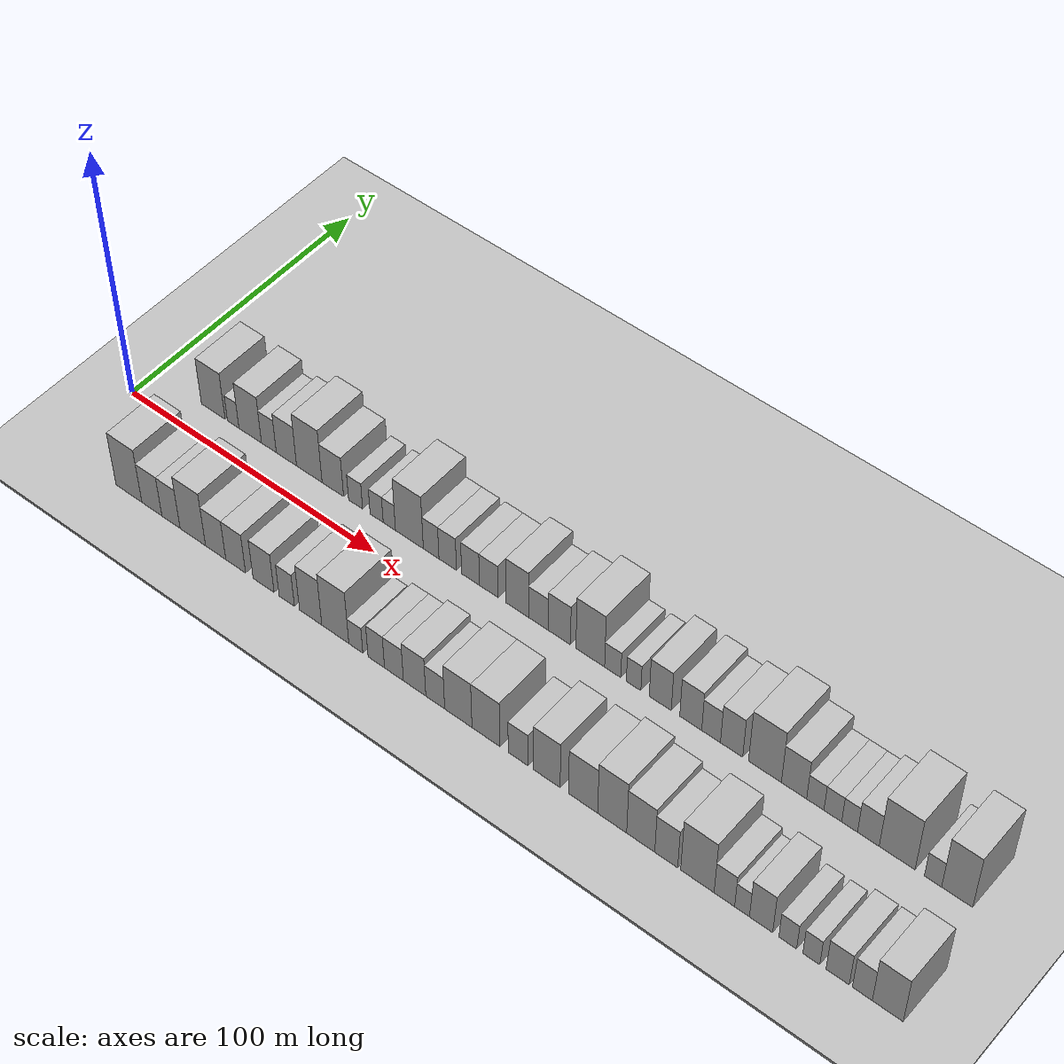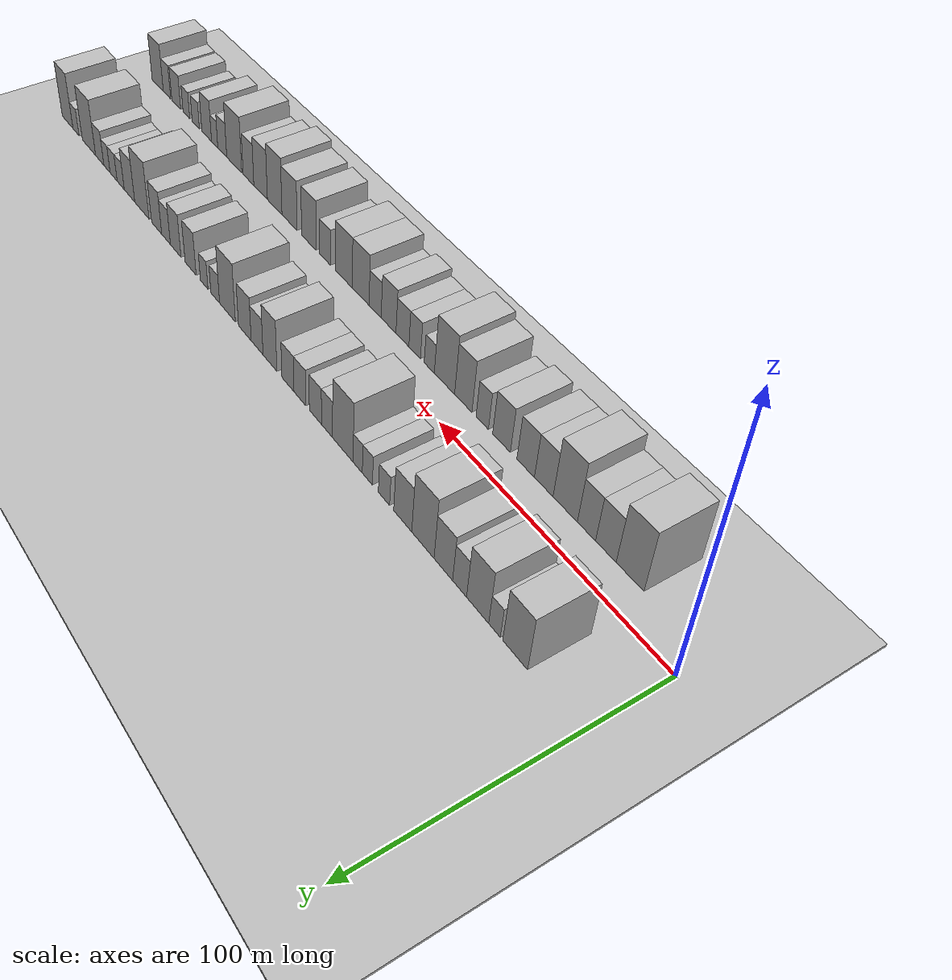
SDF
<?xml version="1.0" encoding="utf-8"?>

<sdf version="1.6">

   <world name="default">

      <gui fullscreen="0">

         <camera name="user_camera">

            <pose>-15 0 4.57585 0 0 0</pose>

            <view_controller>orbit</view_controller>

         </camera>

      </gui>

      <scene>

         <sky>

           <clouds>

             <speed>12</speed>

           </clouds>

         </sky>

         <ambient>0.4 0.4 0.4 1</ambient>

         <background>0.7 0.7 0.7 1</background>

         <shadows>1</shadows>

      </scene>

      <gravity>0 0 -9.8066</gravity>

      <magnetic_field>6e-06 2.3e-05 -4.2e-05</magnetic_field>

      <physics default="0" name="default_physics" type="ode">

         <ode>

            <solver>

               <type>quick</type>

               <iters>10</iters>

               <sor>1.0</sor>

               <use_dynamic_moi_rescaling>0</use_dynamic_moi_rescaling>

            </solver>

            <constraints>

               <cfm>0</cfm>

               <erp>0.2</erp>

               <contact_max_correcting_vel>100</contact_max_correcting_vel>

               <contact_surface_layer>0.001</contact_surface_layer>

            </constraints>

         </ode>

         <max_step_size>0.004</max_step_size>

         <real_time_factor>1</real_time_factor>

         <real_time_update_rate>250</real_time_update_rate>

      </physics>

      <light name="sun" type="directional">

         <cast_shadows>1</cast_shadows>

         <pose>0 0 10 0 0 0</pose>

         <diffuse>0.8 0.8 0.8 1</diffuse>

         <specular>0.2 0.2 0.2 1</specular>

         <attenuation>

            <range>1000</range>

            <constant>0.9</constant>

            <linear>0.01</linear>

            <quadratic>0.001</quadratic>

         </attenuation>

         <direction>-0.5 0.1 -0.9</direction>

      </light>

      <include>

         <name>ground_plane_1</name>

         <uri>model://HANNAS_ground_plane</uri>

         <pose>0 0 0  0 0 0</pose>

      </include>

      <include>

         <name>ground_plane_2</name>

         <uri>model://HANNAS_ground_plane</uri>

         <pose>100 0 0  0 0 0</pose>

      </include>

      <model name="building_1">

         <static>1</static>

         <pose frame="">25.0306 20.0000 0 0.000000 0.000000 1.570796</pose>

         <link name="link">

            <pose frame="">0 0 10.50 0 0 0</pose>

            <collision name="collision">

               <geometry>

                  <box>

                     <size>20.0000 10.0612 21.0000</size>

                  </box>

               </geometry>

               <max_contacts>10</max_contacts>

               <surface>

                  <contact>

                     <ode/>

                  </contact>

                  <bounce/>

                  <friction>

                     <torsional>

                        <ode/>

                     </torsional>

                     <ode/>

                  </friction>

               </surface>

            </collision>

            <visual name="visual">

               <cast_shadows>0</cast_shadows>

               <geometry>

                  <box>

                     <size>20.0000 10.0612 21.0000</size>

                  </box>

               </geometry>

               <material>

                  <script>

                     <uri>model://HANNAS_wall/materials/scripts</uri>

                     <uri>model://HANNAS_wall/materials/textures</uri>

                     <name>vrc/HANNAS_wall</name>

                  </script>

               </material>

            </visual>

            <self_collide>0</self_collide>

            <enable_wind>0</enable_wind>

            <kinematic>0</kinematic>

         </link>

      </model>

      <model name="building_2">

         <static>1</static>

         <pose frame="">33.4875 20.0000 0 0.000000 0.000000 1.570796</pose>

         <link name="link">

            <pose frame="">0 0 6.00 0 0 0</pose>

            <collision name="collision">

               <geometry>

                  <box>

                     <size>20.0000 4.8526 12.0000</size>

                  </box>

               </geometry>

               <max_contacts>10</max_contacts>

               <surface>

                  <contact>

                     <ode/>

                  </contact>

                  <bounce/>

                  <friction>

                     <torsional>

                        <ode/>

                     </torsional>

                     <ode/>

                  </friction>

               </surface>

            </collision>

            <visual name="visual">

               <cast_shadows>0</cast_shadows>

               <geometry>

                  <box>

                     <size>20.0000 4.8526 12.0000</size>

                  </box>

               </geometry>

               <material>

                  <script>

                     <uri>model://HANNAS_wall/materials/scripts</uri>

                     <uri>model://HANNAS_wall/materials/textures</uri>

                     <name>vrc/HANNAS_wall</name>

                  </script>

               </material>

            </visual>

            <self_collide>0</self_collide>

            <enable_wind>0</enable_wind>

            <kinematic>0</kinematic>

         </link>

      </model>

      <model name="building_3">

         <static>1</static>

         <pose frame="">40.6501 20.0000 0 0.000000 0.000000 1.570796</pose>

         <link name="link">

            <pose frame="">0 0 10.50 0 0 0</pose>

            <collision name="collision">

               <geometry>

                  <box>

                     <size>20.0000 9.4726 21.0000</size>

                  </box>

               </geometry>

               <max_contacts>10</max_contacts>

               <surface>

                  <contact>

                     <ode/>

                  </contact>

                  <bounce/>

                  <friction>

                     <torsional>

                        <ode/>

                     </torsional>

                     <ode/>

                  </friction>

               </surface>

            </collision>

            <visual name="visual">

               <cast_shadows>0</cast_shadows>

               <geometry>

                  <box>

                     <size>20.0000 9.4726 21.0000</size>

                  </box>

               </geometry>

               <material>

                  <script>

                     <uri>model://HANNAS_wall/materials/scripts</uri>

                     <uri>model://HANNAS_wall/materials/textures</uri>

                     <name>vrc/HANNAS_wall</name>

                  </script>

               </material>

            </visual>

            <self_collide>0</self_collide>

            <enable_wind>0</enable_wind>

            <kinematic>0</kinematic>

         </link>

      </model>

      <model name="building_4">

         <static>1</static>

         <pose frame="">48.4580 20.0000 0 0.000000 0.000000 1.570796</pose>

         <link name="link">

            <pose frame="">0 0 7.50 0 0 0</pose>

            <collision name="collision">

               <geometry>

                  <box>

                     <size>20.0000 6.1433 15.0000</size>

                  </box>

               </geometry>

               <max_contacts>10</max_contacts>

               <surface>

                  <contact>

                     <ode/>

                  </contact>

                  <bounce/>

                  <friction>

                     <torsional>

                        <ode/>

                     </torsional>

                     <ode/>

                  </friction>

               </surface>

            </collision>

            <visual name="visual">

               <cast_shadows>0</cast_shadows>

               <geometry>

                  <box>

                     <size>20.0000 6.1433 15.0000</size>

                  </box>

               </geometry>

               <material>

                  <script>

                     <uri>model://HANNAS_wall/materials/scripts</uri>

                     <uri>model://HANNAS_wall/materials/textures</uri>

                     <name>vrc/HANNAS_wall</name>

                  </script>

               </material>

            </visual>

            <self_collide>0</self_collide>

            <enable_wind>0</enable_wind>

            <kinematic>0</kinematic>

         </link>

      </model>

      <model name="building_5">

         <static>1</static>

         <pose frame="">55.7201 20.0000 0 0.000000 0.000000 1.570796</pose>

         <link name="link">

            <pose frame="">0 0 9.00 0 0 0</pose>

            <collision name="collision">

               <geometry>

                  <box>

                     <size>20.0000 8.3807 18.0000</size>

                  </box>

               </geometry>

               <max_contacts>10</max_contacts>

               <surface>

                  <contact>

                     <ode/>

                  </contact>

                  <bounce/>

                  <friction>

                     <torsional>

                        <ode/>

                     </torsional>

                     <ode/>

                  </friction>

               </surface>

            </collision>

            <visual name="visual">

               <cast_shadows>0</cast_shadows>

               <geometry>

                  <box>

                     <size>20.0000 8.3807 18.0000</size>

                  </box>

               </geometry>

               <material>

                  <script>

                     <uri>model://HANNAS_wall/materials/scripts</uri>

                     <uri>model://HANNAS_wall/materials/textures</uri>

                     <name>vrc/HANNAS_wall</name>

                  </script>

               </material>

            </visual>

            <self_collide>0</self_collide>

            <enable_wind>0</enable_wind>

            <kinematic>0</kinematic>

         </link>

      </model>

      <model name="building_6">

         <static>1</static>

         <pose frame="">65.1428 20.0000 0 0.000000 0.000000 1.570796</pose>

         <link name="link">

            <pose frame="">0 0 12.00 0 0 0</pose>

            <collision name="collision">

               <geometry>

                  <box>

                     <size>20.0000 10.4647 24.0000</size>

                  </box>

               </geometry>

               <max_contacts>10</max_contacts>

               <surface>

                  <contact>

                     <ode/>

                  </contact>

                  <bounce/>

                  <friction>

                     <torsional>

                        <ode/>

                     </torsional>

                     <ode/>

                  </friction>

               </surface>

            </collision>

            <visual name="visual">

               <cast_shadows>0</cast_shadows>

               <geometry>

                  <box>

                     <size>20.0000 10.4647 24.0000</size>

                  </box>

               </geometry>

               <material>

                  <script>

                     <uri>model://HANNAS_wall/materials/scripts</uri>

                     <uri>model://HANNAS_wall/materials/textures</uri>

                     <name>vrc/HANNAS_wall</name>

                  </script>

               </material>

            </visual>

            <self_collide>0</self_collide>

            <enable_wind>0</enable_wind>

            <kinematic>0</kinematic>

         </link>

      </model>

      <model name="building_7">

         <static>1</static>

         <pose frame="">74.7315 20.0000 0 0.000000 0.000000 1.570796</pose>

         <link name="link">

            <pose frame="">0 0 9.00 0 0 0</pose>

            <collision name="collision">

               <geometry>

                  <box>

                     <size>20.0000 8.7126 18.0000</size>

                  </box>

               </geometry>

               <max_contacts>10</max_contacts>

               <surface>

                  <contact>

                     <ode/>

                  </contact>

                  <bounce/>

                  <friction>

                     <torsional>

                        <ode/>

                     </torsional>

                     <ode/>

                  </friction>

               </surface>

            </collision>

            <visual name="visual">

               <cast_shadows>0</cast_shadows>

               <geometry>

                  <box>

                     <size>20.0000 8.7126 18.0000</size>

                  </box>

               </geometry>

               <material>

                  <script>

                     <uri>model://HANNAS_wall/materials/scripts</uri>

                     <uri>model://HANNAS_wall/materials/textures</uri>

                     <name>vrc/HANNAS_wall</name>

                  </script>

               </material>

            </visual>

            <self_collide>0</self_collide>

            <enable_wind>0</enable_wind>

            <kinematic>0</kinematic>

         </link>

      </model>

      <model name="building_8">

         <static>1</static>

         <pose frame="">83.9068 20.0000 0 0.000000 0.000000 1.570796</pose>

         <link name="link">

            <pose frame="">0 0 6.00 0 0 0</pose>

            <collision name="collision">

               <geometry>

                  <box>

                     <size>20.0000 5.6382 12.0000</size>

                  </box>

               </geometry>

               <max_contacts>10</max_contacts>

               <surface>

                  <contact>

                     <ode/>

                  </contact>

                  <bounce/>

                  <friction>

                     <torsional>

                        <ode/>

                     </torsional>

                     <ode/>

                  </friction>

               </surface>

            </collision>

            <visual name="visual">

               <cast_shadows>0</cast_shadows>

               <geometry>

                  <box>

                     <size>20.0000 5.6382 12.0000</size>

                  </box>

               </geometry>

               <material>

                  <script>

                     <uri>model://HANNAS_wall/materials/scripts</uri>

                     <uri>model://HANNAS_wall/materials/textures</uri>

                     <name>vrc/HANNAS_wall</name>

                  </script>

               </material>

            </visual>

            <self_collide>0</self_collide>

            <enable_wind>0</enable_wind>

            <kinematic>0</kinematic>

         </link>

      </model>

      <model name="building_9">

         <static>1</static>

         <pose frame="">92.3290 20.0000 0 0.000000 0.000000 1.570796</pose>

         <link name="link">

            <pose frame="">0 0 6.00 0 0 0</pose>

            <collision name="collision">

               <geometry>

                  <box>

                     <size>20.0000 5.2062 12.0000</size>

                  </box>

               </geometry>

               <max_contacts>10</max_contacts>

               <surface>

                  <contact>

                     <ode/>

                  </contact>

                  <bounce/>

                  <friction>

                     <torsional>

                        <ode/>

                     </torsional>

                     <ode/>

                  </friction>

               </surface>

            </collision>

            <visual name="visual">

               <cast_shadows>0</cast_shadows>

               <geometry>

                  <box>

                     <size>20.0000 5.2062 12.0000</size>

                  </box>

               </geometry>

               <material>

                  <script>

                     <uri>model://HANNAS_wall/materials/scripts</uri>

                     <uri>model://HANNAS_wall/materials/textures</uri>

                     <name>vrc/HANNAS_wall</name>

                  </script>

               </material>

            </visual>

            <self_collide>0</self_collide>

            <enable_wind>0</enable_wind>

            <kinematic>0</kinematic>

         </link>

      </model>

      <model name="building_10">

         <static>1</static>

         <pose frame="">97.3606 20.0000 0 0.000000 0.000000 1.570796</pose>

         <link name="link">

            <pose frame="">0 0 6.00 0 0 0</pose>

            <collision name="collision">

               <geometry>

                  <box>

                     <size>20.0000 4.8569 12.0000</size>

                  </box>

               </geometry>

               <max_contacts>10</max_contacts>

               <surface>

                  <contact>

                     <ode/>

                  </contact>

                  <bounce/>

                  <friction>

                     <torsional>

                        <ode/>

                     </torsional>

                     <ode/>

                  </friction>

               </surface>

            </collision>

            <visual name="visual">

               <cast_shadows>0</cast_shadows>

               <geometry>

                  <box>

                     <size>20.0000 4.8569 12.0000</size>

                  </box>

               </geometry>

               <material>

                  <script>

                     <uri>model://HANNAS_wall/materials/scripts</uri>

                     <uri>model://HANNAS_wall/materials/textures</uri>

                     <name>vrc/HANNAS_wall</name>

                  </script>

               </material>

            </visual>

            <self_collide>0</self_collide>

            <enable_wind>0</enable_wind>

            <kinematic>0</kinematic>

         </link>

      </model>

      <model name="building_11">

         <static>1</static>

         <pose frame="">105.2721 20.0000 0 0.000000 0.000000 1.570796</pose>

         <link name="link">

            <pose frame="">0 0 12.00 0 0 0</pose>

            <collision name="collision">

               <geometry>

                  <box>

                     <size>20.0000 10.9661 24.0000</size>

                  </box>

               </geometry>

               <max_contacts>10</max_contacts>

               <surface>

                  <contact>

                     <ode/>

                  </contact>

                  <bounce/>

                  <friction>

                     <torsional>

                        <ode/>

                     </torsional>

                     <ode/>

                  </friction>

               </surface>

            </collision>

            <visual name="visual">

               <cast_shadows>0</cast_shadows>

               <geometry>

                  <box>

                     <size>20.0000 10.9661 24.0000</size>

                  </box>

               </geometry>

               <material>

                  <script>

                     <uri>model://HANNAS_wall/materials/scripts</uri>

                     <uri>model://HANNAS_wall/materials/textures</uri>

                     <name>vrc/HANNAS_wall</name>

                  </script>

               </material>

            </visual>

            <self_collide>0</self_collide>

            <enable_wind>0</enable_wind>

            <kinematic>0</kinematic>

         </link>

      </model>

      <model name="building_12">

         <static>1</static>

         <pose frame="">113.7938 20.0000 0 0.000000 0.000000 1.570796</pose>

         <link name="link">

            <pose frame="">0 0 7.50 0 0 0</pose>

            <collision name="collision">

               <geometry>

                  <box>

                     <size>20.0000 6.0773 15.0000</size>

                  </box>

               </geometry>

               <max_contacts>10</max_contacts>

               <surface>

                  <contact>

                     <ode/>

                  </contact>

                  <bounce/>

                  <friction>

                     <torsional>

                        <ode/>

                     </torsional>

                     <ode/>

                  </friction>

               </surface>

            </collision>

            <visual name="visual">

               <cast_shadows>0</cast_shadows>

               <geometry>

                  <box>

                     <size>20.0000 6.0773 15.0000</size>

                  </box>

               </geometry>

               <material>

                  <script>

                     <uri>model://HANNAS_wall/materials/scripts</uri>

                     <uri>model://HANNAS_wall/materials/textures</uri>

                     <name>vrc/HANNAS_wall</name>

                  </script>

               </material>

            </visual>

            <self_collide>0</self_collide>

            <enable_wind>0</enable_wind>

            <kinematic>0</kinematic>

         </link>

      </model>

      <model name="building_13">

         <static>1</static>

         <pose frame="">120.2307 20.0000 0 0.000000 0.000000 1.570796</pose>

         <link name="link">

            <pose frame="">0 0 7.50 0 0 0</pose>

            <collision name="collision">

               <geometry>

                  <box>

                     <size>20.0000 6.7966 15.0000</size>

                  </box>

               </geometry>

               <max_contacts>10</max_contacts>

               <surface>

                  <contact>

                     <ode/>

                  </contact>

                  <bounce/>

                  <friction>

                     <torsional>

                        <ode/>

                     </torsional>

                     <ode/>

                  </friction>

               </surface>

            </collision>

            <visual name="visual">

               <cast_shadows>0</cast_shadows>

               <geometry>

                  <box>

                     <size>20.0000 6.7966 15.0000</size>

                  </box>

               </geometry>

               <material>

                  <script>

                     <uri>model://HANNAS_wall/materials/scripts</uri>

                     <uri>model://HANNAS_wall/materials/textures</uri>

                     <name>vrc/HANNAS_wall</name>

                  </script>

               </material>

            </visual>

            <self_collide>0</self_collide>

            <enable_wind>0</enable_wind>

            <kinematic>0</kinematic>

         </link>

      </model>

      <model name="building_14">

         <static>1</static>

         <pose frame="">129.0535 20.0000 0 0.000000 0.000000 1.570796</pose>

         <link name="link">

            <pose frame="">0 0 7.50 0 0 0</pose>

            <collision name="collision">

               <geometry>

                  <box>

                     <size>20.0000 6.8490 15.0000</size>

                  </box>

               </geometry>

               <max_contacts>10</max_contacts>

               <surface>

                  <contact>

                     <ode/>

                  </contact>

                  <bounce/>

                  <friction>

                     <torsional>

                        <ode/>

                     </torsional>

                     <ode/>

                  </friction>

               </surface>

            </collision>

            <visual name="visual">

               <cast_shadows>0</cast_shadows>

               <geometry>

                  <box>

                     <size>20.0000 6.8490 15.0000</size>

                  </box>

               </geometry>

               <material>

                  <script>

                     <uri>model://HANNAS_wall/materials/scripts</uri>

                     <uri>model://HANNAS_wall/materials/textures</uri>

                     <name>vrc/HANNAS_wall</name>

                  </script>

               </material>

            </visual>

            <self_collide>0</self_collide>

            <enable_wind>0</enable_wind>

            <kinematic>0</kinematic>

         </link>

      </model>

      <model name="building_15">

         <static>1</static>

         <pose frame="">136.0422 20.0000 0 0.000000 0.000000 1.570796</pose>

         <link name="link">

            <pose frame="">0 0 7.50 0 0 0</pose>

            <collision name="collision">

               <geometry>

                  <box>

                     <size>20.0000 7.1284 15.0000</size>

                  </box>

               </geometry>

               <max_contacts>10</max_contacts>

               <surface>

                  <contact>

                     <ode/>

                  </contact>

                  <bounce/>

                  <friction>

                     <torsional>

                        <ode/>

                     </torsional>

                     <ode/>

                  </friction>

               </surface>

            </collision>

            <visual name="visual">

               <cast_shadows>0</cast_shadows>

               <geometry>

                  <box>

                     <size>20.0000 7.1284 15.0000</size>

                  </box>

               </geometry>

               <material>

                  <script>

                     <uri>model://HANNAS_wall/materials/scripts</uri>

                     <uri>model://HANNAS_wall/materials/textures</uri>

                     <name>vrc/HANNAS_wall</name>

                  </script>

               </material>

            </visual>

            <self_collide>0</self_collide>

            <enable_wind>0</enable_wind>

            <kinematic>0</kinematic>

         </link>

      </model>

      <model name="building_16">

         <static>1</static>

         <pose frame="">146.8464 20.0000 0 0.000000 0.000000 1.570796</pose>

         <link name="link">

            <pose frame="">0 0 10.50 0 0 0</pose>

            <collision name="collision">

               <geometry>

                  <box>

                     <size>20.0000 8.4800 21.0000</size>

                  </box>

               </geometry>

               <max_contacts>10</max_contacts>

               <surface>

                  <contact>

                     <ode/>

                  </contact>

                  <bounce/>

                  <friction>

                     <torsional>

                        <ode/>

                     </torsional>

                     <ode/>

                  </friction>

               </surface>

            </collision>

            <visual name="visual">

               <cast_shadows>0</cast_shadows>

               <geometry>

                  <box>

                     <size>20.0000 8.4800 21.0000</size>

                  </box>

               </geometry>

               <material>

                  <script>

                     <uri>model://HANNAS_wall/materials/scripts</uri>

                     <uri>model://HANNAS_wall/materials/textures</uri>

                     <name>vrc/HANNAS_wall</name>

                  </script>

               </material>

            </visual>

            <self_collide>0</self_collide>

            <enable_wind>0</enable_wind>

            <kinematic>0</kinematic>

         </link>

      </model>

      <model name="building_17">

         <static>1</static>

         <pose frame="">154.7855 20.0000 0 0.000000 0.000000 1.570796</pose>

         <link name="link">

            <pose frame="">0 0 7.50 0 0 0</pose>

            <collision name="collision">

               <geometry>

                  <box>

                     <size>20.0000 7.3981 15.0000</size>

                  </box>

               </geometry>

               <max_contacts>10</max_contacts>

               <surface>

                  <contact>

                     <ode/>

                  </contact>

                  <bounce/>

                  <friction>

                     <torsional>

                        <ode/>

                     </torsional>

                     <ode/>

                  </friction>

               </surface>

            </collision>

            <visual name="visual">

               <cast_shadows>0</cast_shadows>

               <geometry>

                  <box>

                     <size>20.0000 7.3981 15.0000</size>

                  </box>

               </geometry>

               <material>

                  <script>

                     <uri>model://HANNAS_wall/materials/scripts</uri>

                     <uri>model://HANNAS_wall/materials/textures</uri>

                     <name>vrc/HANNAS_wall</name>

                  </script>

               </material>

            </visual>

            <self_collide>0</self_collide>

            <enable_wind>0</enable_wind>

            <kinematic>0</kinematic>

         </link>

      </model>

      <model name="building_18">

         <static>1</static>

         <pose frame="">162.5635 20.0000 0 0.000000 0.000000 1.570796</pose>

         <link name="link">

            <pose frame="">0 0 9.00 0 0 0</pose>

            <collision name="collision">

               <geometry>

                  <box>

                     <size>20.0000 8.1580 18.0000</size>

                  </box>

               </geometry>

               <max_contacts>10</max_contacts>

               <surface>

                  <contact>

                     <ode/>

                  </contact>

                  <bounce/>

                  <friction>

                     <torsional>

                        <ode/>

                     </torsional>

                     <ode/>

                  </friction>

               </surface>

            </collision>

            <visual name="visual">

               <cast_shadows>0</cast_shadows>

               <geometry>

                  <box>

                     <size>20.0000 8.1580 18.0000</size>

                  </box>

               </geometry>

               <material>

                  <script>

                     <uri>model://HANNAS_wall/materials/scripts</uri>

                     <uri>model://HANNAS_wall/materials/textures</uri>

                     <name>vrc/HANNAS_wall</name>

                  </script>

               </material>

            </visual>

            <self_collide>0</self_collide>

            <enable_wind>0</enable_wind>

            <kinematic>0</kinematic>

         </link>

      </model>

      <model name="building_19">

         <static>1</static>

         <pose frame="">173.8788 20.0000 0 0.000000 0.000000 1.570796</pose>

         <link name="link">

            <pose frame="">0 0 12.00 0 0 0</pose>

            <collision name="collision">

               <geometry>

                  <box>

                     <size>20.0000 10.4726 24.0000</size>

                  </box>

               </geometry>

               <max_contacts>10</max_contacts>

               <surface>

                  <contact>

                     <ode/>

                  </contact>

                  <bounce/>

                  <friction>

                     <torsional>

                        <ode/>

                     </torsional>

                     <ode/>

                  </friction>

               </surface>

            </collision>

            <visual name="visual">

               <cast_shadows>0</cast_shadows>

               <geometry>

                  <box>

                     <size>20.0000 10.4726 24.0000</size>

                  </box>

               </geometry>

               <material>

                  <script>

                     <uri>model://HANNAS_wall/materials/scripts</uri>

                     <uri>model://HANNAS_wall/materials/textures</uri>

                     <name>vrc/HANNAS_wall</name>

                  </script>

               </material>

            </visual>

            <self_collide>0</self_collide>

            <enable_wind>0</enable_wind>

            <kinematic>0</kinematic>

         </link>

      </model>

      <model name="building_20">

         <static>1</static>

         <pose frame="">182.0511 20.0000 0 0.000000 0.000000 1.570796</pose>

         <link name="link">

            <pose frame="">0 0 6.00 0 0 0</pose>

            <collision name="collision">

               <geometry>

                  <box>

                     <size>20.0000 5.8721 12.0000</size>

                  </box>

               </geometry>

               <max_contacts>10</max_contacts>

               <surface>

                  <contact>

                     <ode/>

                  </contact>

                  <bounce/>

                  <friction>

                     <torsional>

                        <ode/>

                     </torsional>

                     <ode/>

                  </friction>

               </surface>

            </collision>

            <visual name="visual">

               <cast_shadows>0</cast_shadows>

               <geometry>

                  <box>

                     <size>20.0000 5.8721 12.0000</size>

                  </box>

               </geometry>

               <material>

                  <script>

                     <uri>model://HANNAS_wall/materials/scripts</uri>

                     <uri>model://HANNAS_wall/materials/textures</uri>

                     <name>vrc/HANNAS_wall</name>

                  </script>

               </material>

            </visual>

            <self_collide>0</self_collide>

            <enable_wind>0</enable_wind>

            <kinematic>0</kinematic>

         </link>

      </model>

      <model name="building_21">

         <static>1</static>

         <pose frame="">189.6062 20.0000 0 0.000000 0.000000 1.570796</pose>

         <link name="link">

            <pose frame="">0 0 6.00 0 0 0</pose>

            <collision name="collision">

               <geometry>

                  <box>

                     <size>20.0000 5.2382 12.0000</size>

                  </box>

               </geometry>

               <max_contacts>10</max_contacts>

               <surface>

                  <contact>

                     <ode/>

                  </contact>

                  <bounce/>

                  <friction>

                     <torsional>

                        <ode/>

                     </torsional>

                     <ode/>

                  </friction>

               </surface>

            </collision>

            <visual name="visual">

               <cast_shadows>0</cast_shadows>

               <geometry>

                  <box>

                     <size>20.0000 5.2382 12.0000</size>

                  </box>

               </geometry>

               <material>

                  <script>

                     <uri>model://HANNAS_wall/materials/scripts</uri>

                     <uri>model://HANNAS_wall/materials/textures</uri>

                     <name>vrc/HANNAS_wall</name>

                  </script>

               </material>

            </visual>

            <self_collide>0</self_collide>

            <enable_wind>0</enable_wind>

            <kinematic>0</kinematic>

         </link>

      </model>

      <model name="building_22">

         <static>1</static>

         <pose frame="">199.1457 20.0000 0 0.000000 0.000000 1.570796</pose>

         <link name="link">

            <pose frame="">0 0 9.00 0 0 0</pose>

            <collision name="collision">

               <geometry>

                  <box>

                     <size>20.0000 7.8409 18.0000</size>

                  </box>

               </geometry>

               <max_contacts>10</max_contacts>

               <surface>

                  <contact>

                     <ode/>

                  </contact>

                  <bounce/>

                  <friction>

                     <torsional>

                        <ode/>

                     </torsional>

                     <ode/>

                  </friction>

               </surface>

            </collision>

            <visual name="visual">

               <cast_shadows>0</cast_shadows>

               <geometry>

                  <box>

                     <size>20.0000 7.8409 18.0000</size>

                  </box>

               </geometry>

               <material>

                  <script>

                     <uri>model://HANNAS_wall/materials/scripts</uri>

                     <uri>model://HANNAS_wall/materials/textures</uri>

                     <name>vrc/HANNAS_wall</name>

                  </script>

               </material>

            </visual>

            <self_collide>0</self_collide>

            <enable_wind>0</enable_wind>

            <kinematic>0</kinematic>

         </link>

      </model>

      <model name="building_23">

         <static>1</static>

         <pose frame="">209.9331 20.0000 0 0.000000 0.000000 1.570796</pose>

         <link name="link">

            <pose frame="">0 0 9.00 0 0 0</pose>

            <collision name="collision">

               <geometry>

                  <box>

                     <size>20.0000 7.7338 18.0000</size>

                  </box>

               </geometry>

               <max_contacts>10</max_contacts>

               <surface>

                  <contact>

                     <ode/>

                  </contact>

                  <bounce/>

                  <friction>

                     <torsional>

                        <ode/>

                     </torsional>

                     <ode/>

                  </friction>

               </surface>

            </collision>

            <visual name="visual">

               <cast_shadows>0</cast_shadows>

               <geometry>

                  <box>

                     <size>20.0000 7.7338 18.0000</size>

                  </box>

               </geometry>

               <material>

                  <script>

                     <uri>model://HANNAS_wall/materials/scripts</uri>

                     <uri>model://HANNAS_wall/materials/textures</uri>

                     <name>vrc/HANNAS_wall</name>

                  </script>

               </material>

            </visual>

            <self_collide>0</self_collide>

            <enable_wind>0</enable_wind>

            <kinematic>0</kinematic>

         </link>

      </model>

      <model name="building_24">

         <static>1</static>

         <pose frame="">217.0716 20.0000 0 0.000000 0.000000 1.570796</pose>

         <link name="link">

            <pose frame="">0 0 7.50 0 0 0</pose>

            <collision name="collision">

               <geometry>

                  <box>

                     <size>20.0000 6.5432 15.0000</size>

                  </box>

               </geometry>

               <max_contacts>10</max_contacts>

               <surface>

                  <contact>

                     <ode/>

                  </contact>

                  <bounce/>

                  <friction>

                     <torsional>

                        <ode/>

                     </torsional>

                     <ode/>

                  </friction>

               </surface>

            </collision>

            <visual name="visual">

               <cast_shadows>0</cast_shadows>

               <geometry>

                  <box>

                     <size>20.0000 6.5432 15.0000</size>

                  </box>

               </geometry>

               <material>

                  <script>

                     <uri>model://HANNAS_wall/materials/scripts</uri>

                     <uri>model://HANNAS_wall/materials/textures</uri>

                     <name>vrc/HANNAS_wall</name>

                  </script>

               </material>

            </visual>

            <self_collide>0</self_collide>

            <enable_wind>0</enable_wind>

            <kinematic>0</kinematic>

         </link>

      </model>

      <model name="building_25">

         <static>1</static>

         <pose frame="">224.2039 20.0000 0 0.000000 0.000000 1.570796</pose>

         <link name="link">

            <pose frame="">0 0 9.00 0 0 0</pose>

            <collision name="collision">

               <geometry>

                  <box>

                     <size>20.0000 7.7216 18.0000</size>

                  </box>

               </geometry>

               <max_contacts>10</max_contacts>

               <surface>

                  <contact>

                     <ode/>

                  </contact>

                  <bounce/>

                  <friction>

                     <torsional>

                        <ode/>

                     </torsional>

                     <ode/>

                  </friction>

               </surface>

            </collision>

            <visual name="visual">

               <cast_shadows>0</cast_shadows>

               <geometry>

                  <box>

                     <size>20.0000 7.7216 18.0000</size>

                  </box>

               </geometry>

               <material>

                  <script>

                     <uri>model://HANNAS_wall/materials/scripts</uri>

                     <uri>model://HANNAS_wall/materials/textures</uri>

                     <name>vrc/HANNAS_wall</name>

                  </script>

               </material>

            </visual>

            <self_collide>0</self_collide>

            <enable_wind>0</enable_wind>

            <kinematic>0</kinematic>

         </link>

      </model>

      <model name="building_26">

         <static>1</static>

         <pose frame="">235.6873 20.0000 0 0.000000 0.000000 1.570796</pose>

         <link name="link">

            <pose frame="">0 0 12.00 0 0 0</pose>

            <collision name="collision">

               <geometry>

                  <box>

                     <size>20.0000 11.2451 24.0000</size>

                  </box>

               </geometry>

               <max_contacts>10</max_contacts>

               <surface>

                  <contact>

                     <ode/>

                  </contact>

                  <bounce/>

                  <friction>

                     <torsional>

                        <ode/>

                     </torsional>

                     <ode/>

                  </friction>

               </surface>

            </collision>

            <visual name="visual">

               <cast_shadows>0</cast_shadows>

               <geometry>

                  <box>

                     <size>20.0000 11.2451 24.0000</size>

                  </box>

               </geometry>

               <material>

                  <script>

                     <uri>model://HANNAS_wall/materials/scripts</uri>

                     <uri>model://HANNAS_wall/materials/textures</uri>

                     <name>vrc/HANNAS_wall</name>

                  </script>

               </material>

            </visual>

            <self_collide>0</self_collide>

            <enable_wind>0</enable_wind>

            <kinematic>0</kinematic>

         </link>

      </model>

      <model name="building_27">

         <static>1</static>

         <pose frame="">245.5917 20.0000 0 0.000000 0.000000 1.570796</pose>

         <link name="link">

            <pose frame="">0 0 9.00 0 0 0</pose>

            <collision name="collision">

               <geometry>

                  <box>

                     <size>20.0000 8.5637 18.0000</size>

                  </box>

               </geometry>

               <max_contacts>10</max_contacts>

               <surface>

                  <contact>

                     <ode/>

                  </contact>

                  <bounce/>

                  <friction>

                     <torsional>

                        <ode/>

                     </torsional>

                     <ode/>

                  </friction>

               </surface>

            </collision>

            <visual name="visual">

               <cast_shadows>0</cast_shadows>

               <geometry>

                  <box>

                     <size>20.0000 8.5637 18.0000</size>

                  </box>

               </geometry>

               <material>

                  <script>

                     <uri>model://HANNAS_wall/materials/scripts</uri>

                     <uri>model://HANNAS_wall/materials/textures</uri>

                     <name>vrc/HANNAS_wall</name>

                  </script>

               </material>

            </visual>

            <self_collide>0</self_collide>

            <enable_wind>0</enable_wind>

            <kinematic>0</kinematic>

         </link>

      </model>

      <model name="building_28">

         <static>1</static>

         <pose frame="">252.7836 20.0000 0 0.000000 0.000000 1.570796</pose>

         <link name="link">

            <pose frame="">0 0 6.00 0 0 0</pose>

            <collision name="collision">

               <geometry>

                  <box>

                     <size>20.0000 5.8200 12.0000</size>

                  </box>

               </geometry>

               <max_contacts>10</max_contacts>

               <surface>

                  <contact>

                     <ode/>

                  </contact>

                  <bounce/>

                  <friction>

                     <torsional>

                        <ode/>

                     </torsional>

                     <ode/>

                  </friction>

               </surface>

            </collision>

            <visual name="visual">

               <cast_shadows>0</cast_shadows>

               <geometry>

                  <box>

                     <size>20.0000 5.8200 12.0000</size>

                  </box>

               </geometry>

               <material>

                  <script>

                     <uri>model://HANNAS_wall/materials/scripts</uri>

                     <uri>model://HANNAS_wall/materials/textures</uri>

                     <name>vrc/HANNAS_wall</name>

                  </script>

               </material>

            </visual>

            <self_collide>0</self_collide>

            <enable_wind>0</enable_wind>

            <kinematic>0</kinematic>

         </link>

      </model>

      <model name="building_29">

         <static>1</static>

         <pose frame="">258.6537 20.0000 0 0.000000 0.000000 1.570796</pose>

         <link name="link">

            <pose frame="">0 0 6.00 0 0 0</pose>

            <collision name="collision">

               <geometry>

                  <box>

                     <size>20.0000 5.9202 12.0000</size>

                  </box>

               </geometry>

               <max_contacts>10</max_contacts>

               <surface>

                  <contact>

                     <ode/>

                  </contact>

                  <bounce/>

                  <friction>

                     <torsional>

                        <ode/>

                     </torsional>

                     <ode/>

                  </friction>

               </surface>

            </collision>

            <visual name="visual">

               <cast_shadows>0</cast_shadows>

               <geometry>

                  <box>

                     <size>20.0000 5.9202 12.0000</size>

                  </box>

               </geometry>

               <material>

                  <script>

                     <uri>model://HANNAS_wall/materials/scripts</uri>

                     <uri>model://HANNAS_wall/materials/textures</uri>

                     <name>vrc/HANNAS_wall</name>

                  </script>

               </material>

            </visual>

            <self_collide>0</self_collide>

            <enable_wind>0</enable_wind>

            <kinematic>0</kinematic>

         </link>

      </model>

      <model name="building_30">

         <static>1</static>

         <pose frame="">264.2388 20.0000 0 0.000000 0.000000 1.570796</pose>

         <link name="link">

            <pose frame="">0 0 6.00 0 0 0</pose>

            <collision name="collision">

               <geometry>

                  <box>

                     <size>20.0000 5.2501 12.0000</size>

                  </box>

               </geometry>

               <max_contacts>10</max_contacts>

               <surface>

                  <contact>

                     <ode/>

                  </contact>

                  <bounce/>

                  <friction>

                     <torsional>

                        <ode/>

                     </torsional>

                     <ode/>

                  </friction>

               </surface>

            </collision>

            <visual name="visual">

               <cast_shadows>0</cast_shadows>

               <geometry>

                  <box>

                     <size>20.0000 5.2501 12.0000</size>

                  </box>

               </geometry>

               <material>

                  <script>

                     <uri>model://HANNAS_wall/materials/scripts</uri>

                     <uri>model://HANNAS_wall/materials/textures</uri>

                     <name>vrc/HANNAS_wall</name>

                  </script>

               </material>

            </visual>

            <self_collide>0</self_collide>

            <enable_wind>0</enable_wind>

            <kinematic>0</kinematic>

         </link>

      </model>

      <model name="building_31">

         <static>1</static>

         <pose frame="">270.4426 20.0000 0 0.000000 0.000000 1.570796</pose>

         <link name="link">

            <pose frame="">0 0 7.50 0 0 0</pose>

            <collision name="collision">

               <geometry>

                  <box>

                     <size>20.0000 7.1574 15.0000</size>

                  </box>

               </geometry>

               <max_contacts>10</max_contacts>

               <surface>

                  <contact>

                     <ode/>

                  </contact>

                  <bounce/>

                  <friction>

                     <torsional>

                        <ode/>

                     </torsional>

                     <ode/>

                  </friction>

               </surface>

            </collision>

            <visual name="visual">

               <cast_shadows>0</cast_shadows>

               <geometry>

                  <box>

                     <size>20.0000 7.1574 15.0000</size>

                  </box>

               </geometry>

               <material>

                  <script>

                     <uri>model://HANNAS_wall/materials/scripts</uri>

                     <uri>model://HANNAS_wall/materials/textures</uri>

                     <name>vrc/HANNAS_wall</name>

                  </script>

               </material>

            </visual>

            <self_collide>0</self_collide>

            <enable_wind>0</enable_wind>

            <kinematic>0</kinematic>

         </link>

      </model>

      <model name="building_32">

         <static>1</static>

         <pose frame="">279.8806 20.0000 0 0.000000 0.000000 1.570796</pose>

         <link name="link">

            <pose frame="">0 0 12.00 0 0 0</pose>

            <collision name="collision">

               <geometry>

                  <box>

                     <size>20.0000 11.7185 24.0000</size>

                  </box>

               </geometry>

               <max_contacts>10</max_contacts>

               <surface>

                  <contact>

                     <ode/>

                  </contact>

                  <bounce/>

                  <friction>

                     <torsional>

                        <ode/>

                     </torsional>

                     <ode/>

                  </friction>

               </surface>

            </collision>

            <visual name="visual">

               <cast_shadows>0</cast_shadows>

               <geometry>

                  <box>

                     <size>20.0000 11.7185 24.0000</size>

                  </box>

               </geometry>

               <material>

                  <script>

                     <uri>model://HANNAS_wall/materials/scripts</uri>

                     <uri>model://HANNAS_wall/materials/textures</uri>

                     <name>vrc/HANNAS_wall</name>

                  </script>

               </material>

            </visual>

            <self_collide>0</self_collide>

            <enable_wind>0</enable_wind>

            <kinematic>0</kinematic>

         </link>

      </model>

      <model name="building_33">

         <static>1</static>

         <pose frame="">291.5039 20.0000 0 0.000000 0.000000 1.570796</pose>

         <link name="link">

            <pose frame="">0 0 6.00 0 0 0</pose>

            <collision name="collision">

               <geometry>

                  <box>

                     <size>20.0000 5.5281 12.0000</size>

                  </box>

               </geometry>

               <max_contacts>10</max_contacts>

               <surface>

                  <contact>

                     <ode/>

                  </contact>

                  <bounce/>

                  <friction>

                     <torsional>

                        <ode/>

                     </torsional>

                     <ode/>

                  </friction>

               </surface>

            </collision>

            <visual name="visual">

               <cast_shadows>0</cast_shadows>

               <geometry>

                  <box>

                     <size>20.0000 5.5281 12.0000</size>

                  </box>

               </geometry>

               <material>

                  <script>

                     <uri>model://HANNAS_wall/materials/scripts</uri>

                     <uri>model://HANNAS_wall/materials/textures</uri>

                     <name>vrc/HANNAS_wall</name>

                  </script>

               </material>

            </visual>

            <self_collide>0</self_collide>

            <enable_wind>0</enable_wind>

            <kinematic>0</kinematic>

         </link>

      </model>

      <model name="building_34">

         <static>1</static>

         <pose frame="">299.2291 20.0000 0 0.000000 0.000000 1.570796</pose>

         <link name="link">

            <pose frame="">0 0 12.00 0 0 0</pose>

            <collision name="collision">

               <geometry>

                  <box>

                     <size>20.0000 9.9224 24.0000</size>

                  </box>

               </geometry>

               <max_contacts>10</max_contacts>

               <surface>

                  <contact>

                     <ode/>

                  </contact>

                  <bounce/>

                  <friction>

                     <torsional>

                        <ode/>

                     </torsional>

                     <ode/>

                  </friction>

               </surface>

            </collision>

            <visual name="visual">

               <cast_shadows>0</cast_shadows>

               <geometry>

                  <box>

                     <size>20.0000 9.9224 24.0000</size>

                  </box>

               </geometry>

               <material>

                  <script>

                     <uri>model://HANNAS_wall/materials/scripts</uri>

                     <uri>model://HANNAS_wall/materials/textures</uri>

                     <name>vrc/HANNAS_wall</name>

                  </script>

               </material>

            </visual>

            <self_collide>0</self_collide>

            <enable_wind>0</enable_wind>

            <kinematic>0</kinematic>

         </link>

      </model>

      <model name="building_35">

         <static>1</static>

         <pose frame="">28.4641 -20.0000 0 0.000000 0.000000 1.570796</pose>

         <link name="link">

            <pose frame="">0 0 12.00 0 0 0</pose>

            <collision name="collision">

               <geometry>

                  <box>

                     <size>20.0000 10.9283 24.0000</size>

                  </box>

               </geometry>

               <max_contacts>10</max_contacts>

               <surface>

                  <contact>

                     <ode/>

                  </contact>

                  <bounce/>

                  <friction>

                     <torsional>

                        <ode/>

                     </torsional>

                     <ode/>

                  </friction>

               </surface>

            </collision>

            <visual name="visual">

               <cast_shadows>0</cast_shadows>

               <geometry>

                  <box>

                     <size>20.0000 10.9283 24.0000</size>

                  </box>

               </geometry>

               <material>

                  <script>

                     <uri>model://HANNAS_wall/materials/scripts</uri>

                     <uri>model://HANNAS_wall/materials/textures</uri>

                     <name>vrc/HANNAS_wall</name>

                  </script>

               </material>

            </visual>

            <self_collide>0</self_collide>

            <enable_wind>0</enable_wind>

            <kinematic>0</kinematic>

         </link>

      </model>

      <model name="building_36">

         <static>1</static>

         <pose frame="">38.1066 -20.0000 0 0.000000 0.000000 1.570796</pose>

         <link name="link">

            <pose frame="">0 0 9.00 0 0 0</pose>

            <collision name="collision">

               <geometry>

                  <box>

                     <size>20.0000 8.3566 18.0000</size>

                  </box>

               </geometry>

               <max_contacts>10</max_contacts>

               <surface>

                  <contact>

                     <ode/>

                  </contact>

                  <bounce/>

                  <friction>

                     <torsional>

                        <ode/>

                     </torsional>

                     <ode/>

                  </friction>

               </surface>

            </collision>

            <visual name="visual">

               <cast_shadows>0</cast_shadows>

               <geometry>

                  <box>

                     <size>20.0000 8.3566 18.0000</size>

                  </box>

               </geometry>

               <material>

                  <script>

                     <uri>model://HANNAS_wall/materials/scripts</uri>

                     <uri>model://HANNAS_wall/materials/textures</uri>

                     <name>vrc/HANNAS_wall</name>

                  </script>

               </material>

            </visual>

            <self_collide>0</self_collide>

            <enable_wind>0</enable_wind>

            <kinematic>0</kinematic>

         </link>

      </model>

      <model name="building_37">

         <static>1</static>

         <pose frame="">46.0715 -20.0000 0 0.000000 0.000000 1.570796</pose>

         <link name="link">

            <pose frame="">0 0 9.00 0 0 0</pose>

            <collision name="collision">

               <geometry>

                  <box>

                     <size>20.0000 7.5733 18.0000</size>

                  </box>

               </geometry>

               <max_contacts>10</max_contacts>

               <surface>

                  <contact>

                     <ode/>

                  </contact>

                  <bounce/>

                  <friction>

                     <torsional>

                        <ode/>

                     </torsional>

                     <ode/>

                  </friction>

               </surface>

            </collision>

            <visual name="visual">

               <cast_shadows>0</cast_shadows>

               <geometry>

                  <box>

                     <size>20.0000 7.5733 18.0000</size>

                  </box>

               </geometry>

               <material>

                  <script>

                     <uri>model://HANNAS_wall/materials/scripts</uri>

                     <uri>model://HANNAS_wall/materials/textures</uri>

                     <name>vrc/HANNAS_wall</name>

                  </script>

               </material>

            </visual>

            <self_collide>0</self_collide>

            <enable_wind>0</enable_wind>

            <kinematic>0</kinematic>

         </link>

      </model>

      <model name="building_38">

         <static>1</static>

         <pose frame="">55.0820 -20.0000 0 0.000000 0.000000 1.570796</pose>

         <link name="link">

            <pose frame="">0 0 12.00 0 0 0</pose>

            <collision name="collision">

               <geometry>

                  <box>

                     <size>20.0000 10.4478 24.0000</size>

                  </box>

               </geometry>

               <max_contacts>10</max_contacts>

               <surface>

                  <contact>

                     <ode/>

                  </contact>

                  <bounce/>

                  <friction>

                     <torsional>

                        <ode/>

                     </torsional>

                     <ode/>

                  </friction>

               </surface>

            </collision>

            <visual name="visual">

               <cast_shadows>0</cast_shadows>

               <geometry>

                  <box>

                     <size>20.0000 10.4478 24.0000</size>

                  </box>

               </geometry>

               <material>

                  <script>

                     <uri>model://HANNAS_wall/materials/scripts</uri>

                     <uri>model://HANNAS_wall/materials/textures</uri>

                     <name>vrc/HANNAS_wall</name>

                  </script>

               </material>

            </visual>

            <self_collide>0</self_collide>

            <enable_wind>0</enable_wind>

            <kinematic>0</kinematic>

         </link>

      </model>

      <model name="building_39">

         <static>1</static>

         <pose frame="">64.4289 -20.0000 0 0.000000 0.000000 1.570796</pose>

         <link name="link">

            <pose frame="">0 0 9.00 0 0 0</pose>

            <collision name="collision">

               <geometry>

                  <box>

                     <size>20.0000 8.2460 18.0000</size>

                  </box>

               </geometry>

               <max_contacts>10</max_contacts>

               <surface>

                  <contact>

                     <ode/>

                  </contact>

                  <bounce/>

                  <friction>

                     <torsional>

                        <ode/>

                     </torsional>

                     <ode/>

                  </friction>

               </surface>

            </collision>

            <visual name="visual">

               <cast_shadows>0</cast_shadows>

               <geometry>

                  <box>

                     <size>20.0000 8.2460 18.0000</size>

                  </box>

               </geometry>

               <material>

                  <script>

                     <uri>model://HANNAS_wall/materials/scripts</uri>

                     <uri>model://HANNAS_wall/materials/textures</uri>

                     <name>vrc/HANNAS_wall</name>

                  </script>

               </material>

            </visual>

            <self_collide>0</self_collide>

            <enable_wind>0</enable_wind>

            <kinematic>0</kinematic>

         </link>

      </model>

      <model name="building_40">

         <static>1</static>

         <pose frame="">72.5586 -20.0000 0 0.000000 0.000000 1.570796</pose>

         <link name="link">

            <pose frame="">0 0 9.00 0 0 0</pose>

            <collision name="collision">

               <geometry>

                  <box>

                     <size>20.0000 8.0134 18.0000</size>

                  </box>

               </geometry>

               <max_contacts>10</max_contacts>

               <surface>

                  <contact>

                     <ode/>

                  </contact>

                  <bounce/>

                  <friction>

                     <torsional>

                        <ode/>

                     </torsional>

                     <ode/>

                  </friction>

               </surface>

            </collision>

            <visual name="visual">

               <cast_shadows>0</cast_shadows>

               <geometry>

                  <box>

                     <size>20.0000 8.0134 18.0000</size>

                  </box>

               </geometry>

               <material>

                  <script>

                     <uri>model://HANNAS_wall/materials/scripts</uri>

                     <uri>model://HANNAS_wall/materials/textures</uri>

                     <name>vrc/HANNAS_wall</name>

                  </script>

               </material>

            </visual>

            <self_collide>0</self_collide>

            <enable_wind>0</enable_wind>

            <kinematic>0</kinematic>

         </link>

      </model>

      <model name="building_41">

         <static>1</static>

         <pose frame="">83.7648 -20.0000 0 0.000000 0.000000 1.570796</pose>

         <link name="link">

            <pose frame="">0 0 9.00 0 0 0</pose>

            <collision name="collision">

               <geometry>

                  <box>

                     <size>20.0000 8.3991 18.0000</size>

                  </box>

               </geometry>

               <max_contacts>10</max_contacts>

               <surface>

                  <contact>

                     <ode/>

                  </contact>

                  <bounce/>

                  <friction>

                     <torsional>

                        <ode/>

                     </torsional>

                     <ode/>

                  </friction>

               </surface>

            </collision>

            <visual name="visual">

               <cast_shadows>0</cast_shadows>

               <geometry>

                  <box>

                     <size>20.0000 8.3991 18.0000</size>

                  </box>

               </geometry>

               <material>

                  <script>

                     <uri>model://HANNAS_wall/materials/scripts</uri>

                     <uri>model://HANNAS_wall/materials/textures</uri>

                     <name>vrc/HANNAS_wall</name>

                  </script>

               </material>

            </visual>

            <self_collide>0</self_collide>

            <enable_wind>0</enable_wind>

            <kinematic>0</kinematic>

         </link>

      </model>

      <model name="building_42">

         <static>1</static>

         <pose frame="">92.9873 -20.0000 0 0.000000 0.000000 1.570796</pose>

         <link name="link">

            <pose frame="">0 0 7.50 0 0 0</pose>

            <collision name="collision">

               <geometry>

                  <box>

                     <size>20.0000 6.0458 15.0000</size>

                  </box>

               </geometry>

               <max_contacts>10</max_contacts>

               <surface>

                  <contact>

                     <ode/>

                  </contact>

                  <bounce/>

                  <friction>

                     <torsional>

                        <ode/>

                     </torsional>

                     <ode/>

                  </friction>

               </surface>

            </collision>

            <visual name="visual">

               <cast_shadows>0</cast_shadows>

               <geometry>

                  <box>

                     <size>20.0000 6.0458 15.0000</size>

                  </box>

               </geometry>

               <material>

                  <script>

                     <uri>model://HANNAS_wall/materials/scripts</uri>

                     <uri>model://HANNAS_wall/materials/textures</uri>

                     <name>vrc/HANNAS_wall</name>

                  </script>

               </material>

            </visual>

            <self_collide>0</self_collide>

            <enable_wind>0</enable_wind>

            <kinematic>0</kinematic>

         </link>

      </model>

      <model name="building_43">

         <static>1</static>

         <pose frame="">102.3616 -20.0000 0 0.000000 0.000000 1.570796</pose>

         <link name="link">

            <pose frame="">0 0 10.50 0 0 0</pose>

            <collision name="collision">

               <geometry>

                  <box>

                     <size>20.0000 8.7028 21.0000</size>

                  </box>

               </geometry>

               <max_contacts>10</max_contacts>

               <surface>

                  <contact>

                     <ode/>

                  </contact>

                  <bounce/>

                  <friction>

                     <torsional>

                        <ode/>

                     </torsional>

                     <ode/>

                  </friction>

               </surface>

            </collision>

            <visual name="visual">

               <cast_shadows>0</cast_shadows>

               <geometry>

                  <box>

                     <size>20.0000 8.7028 21.0000</size>

                  </box>

               </geometry>

               <material>

                  <script>

                     <uri>model://HANNAS_wall/materials/scripts</uri>

                     <uri>model://HANNAS_wall/materials/textures</uri>

                     <name>vrc/HANNAS_wall</name>

                  </script>

               </material>

            </visual>

            <self_collide>0</self_collide>

            <enable_wind>0</enable_wind>

            <kinematic>0</kinematic>

         </link>

      </model>

      <model name="building_44">

         <static>1</static>

         <pose frame="">111.9658 -20.0000 0 0.000000 0.000000 1.570796</pose>

         <link name="link">

            <pose frame="">0 0 12.00 0 0 0</pose>

            <collision name="collision">

               <geometry>

                  <box>

                     <size>20.0000 10.5055 24.0000</size>

                  </box>

               </geometry>

               <max_contacts>10</max_contacts>

               <surface>

                  <contact>

                     <ode/>

                  </contact>

                  <bounce/>

                  <friction>

                     <torsional>

                        <ode/>

                     </torsional>

                     <ode/>

                  </friction>

               </surface>

            </collision>

            <visual name="visual">

               <cast_shadows>0</cast_shadows>

               <geometry>

                  <box>

                     <size>20.0000 10.5055 24.0000</size>

                  </box>

               </geometry>

               <material>

                  <script>

                     <uri>model://HANNAS_wall/materials/scripts</uri>

                     <uri>model://HANNAS_wall/materials/textures</uri>

                     <name>vrc/HANNAS_wall</name>

                  </script>

               </material>

            </visual>

            <self_collide>0</self_collide>

            <enable_wind>0</enable_wind>

            <kinematic>0</kinematic>

         </link>

      </model>

      <model name="building_45">

         <static>1</static>

         <pose frame="">119.9010 -20.0000 0 0.000000 0.000000 1.570796</pose>

         <link name="link">

            <pose frame="">0 0 6.00 0 0 0</pose>

            <collision name="collision">

               <geometry>

                  <box>

                     <size>20.0000 5.3648 12.0000</size>

                  </box>

               </geometry>

               <max_contacts>10</max_contacts>

               <surface>

                  <contact>

                     <ode/>

                  </contact>

                  <bounce/>

                  <friction>

                     <torsional>

                        <ode/>

                     </torsional>

                     <ode/>

                  </friction>

               </surface>

            </collision>

            <visual name="visual">

               <cast_shadows>0</cast_shadows>

               <geometry>

                  <box>

                     <size>20.0000 5.3648 12.0000</size>

                  </box>

               </geometry>

               <material>

                  <script>

                     <uri>model://HANNAS_wall/materials/scripts</uri>

                     <uri>model://HANNAS_wall/materials/textures</uri>

                     <name>vrc/HANNAS_wall</name>

                  </script>

               </material>

            </visual>

            <self_collide>0</self_collide>

            <enable_wind>0</enable_wind>

            <kinematic>0</kinematic>

         </link>

      </model>

      <model name="building_46">

         <static>1</static>

         <pose frame="">127.7226 -20.0000 0 0.000000 0.000000 1.570796</pose>

         <link name="link">

            <pose frame="">0 0 7.50 0 0 0</pose>

            <collision name="collision">

               <geometry>

                  <box>

                     <size>20.0000 6.2784 15.0000</size>

                  </box>

               </geometry>

               <max_contacts>10</max_contacts>

               <surface>

                  <contact>

                     <ode/>

                  </contact>

                  <bounce/>

                  <friction>

                     <torsional>

                        <ode/>

                     </torsional>

                     <ode/>

                  </friction>

               </surface>

            </collision>

            <visual name="visual">

               <cast_shadows>0</cast_shadows>

               <geometry>

                  <box>

                     <size>20.0000 6.2784 15.0000</size>

                  </box>

               </geometry>

               <material>

                  <script>

                     <uri>model://HANNAS_wall/materials/scripts</uri>

                     <uri>model://HANNAS_wall/materials/textures</uri>

                     <name>vrc/HANNAS_wall</name>

                  </script>

               </material>

            </visual>

            <self_collide>0</self_collide>

            <enable_wind>0</enable_wind>

            <kinematic>0</kinematic>

         </link>

      </model>

      <model name="building_47">

         <static>1</static>

         <pose frame="">134.4351 -20.0000 0 0.000000 0.000000 1.570796</pose>

         <link name="link">

            <pose frame="">0 0 7.50 0 0 0</pose>

            <collision name="collision">

               <geometry>

                  <box>

                     <size>20.0000 7.1467 15.0000</size>

                  </box>

               </geometry>

               <max_contacts>10</max_contacts>

               <surface>

                  <contact>

                     <ode/>

                  </contact>

                  <bounce/>

                  <friction>

                     <torsional>

                        <ode/>

                     </torsional>

                     <ode/>

                  </friction>

               </surface>

            </collision>

            <visual name="visual">

               <cast_shadows>0</cast_shadows>

               <geometry>

                  <box>

                     <size>20.0000 7.1467 15.0000</size>

                  </box>

               </geometry>

               <material>

                  <script>

                     <uri>model://HANNAS_wall/materials/scripts</uri>

                     <uri>model://HANNAS_wall/materials/textures</uri>

                     <name>vrc/HANNAS_wall</name>

                  </script>

               </material>

            </visual>

            <self_collide>0</self_collide>

            <enable_wind>0</enable_wind>

            <kinematic>0</kinematic>

         </link>

      </model>

      <model name="building_48">

         <static>1</static>

         <pose frame="">142.2150 -20.0000 0 0.000000 0.000000 1.570796</pose>

         <link name="link">

            <pose frame="">0 0 9.00 0 0 0</pose>

            <collision name="collision">

               <geometry>

                  <box>

                     <size>20.0000 8.4129 18.0000</size>

                  </box>

               </geometry>

               <max_contacts>10</max_contacts>

               <surface>

                  <contact>

                     <ode/>

                  </contact>

                  <bounce/>

                  <friction>

                     <torsional>

                        <ode/>

                     </torsional>

                     <ode/>

                  </friction>

               </surface>

            </collision>

            <visual name="visual">

               <cast_shadows>0</cast_shadows>

               <geometry>

                  <box>

                     <size>20.0000 8.4129 18.0000</size>

                  </box>

               </geometry>

               <material>

                  <script>

                     <uri>model://HANNAS_wall/materials/scripts</uri>

                     <uri>model://HANNAS_wall/materials/textures</uri>

                     <name>vrc/HANNAS_wall</name>

                  </script>

               </material>

            </visual>

            <self_collide>0</self_collide>

            <enable_wind>0</enable_wind>

            <kinematic>0</kinematic>

         </link>

      </model>

      <model name="building_49">

         <static>1</static>

         <pose frame="">149.9372 -20.0000 0 0.000000 0.000000 1.570796</pose>

         <link name="link">

            <pose frame="">0 0 7.50 0 0 0</pose>

            <collision name="collision">

               <geometry>

                  <box>

                     <size>20.0000 7.0316 15.0000</size>

                  </box>

               </geometry>

               <max_contacts>10</max_contacts>

               <surface>

                  <contact>

                     <ode/>

                  </contact>

                  <bounce/>

                  <friction>

                     <torsional>

                        <ode/>

                     </torsional>

                     <ode/>

                  </friction>

               </surface>

            </collision>

            <visual name="visual">

               <cast_shadows>0</cast_shadows>

               <geometry>

                  <box>

                     <size>20.0000 7.0316 15.0000</size>

                  </box>

               </geometry>

               <material>

                  <script>

                     <uri>model://HANNAS_wall/materials/scripts</uri>

                     <uri>model://HANNAS_wall/materials/textures</uri>

                     <name>vrc/HANNAS_wall</name>

                  </script>

               </material>

            </visual>

            <self_collide>0</self_collide>

            <enable_wind>0</enable_wind>

            <kinematic>0</kinematic>

         </link>

      </model>

      <model name="building_50">

         <static>1</static>

         <pose frame="">158.4925 -20.0000 0 0.000000 0.000000 1.570796</pose>

         <link name="link">

            <pose frame="">0 0 10.50 0 0 0</pose>

            <collision name="collision">

               <geometry>

                  <box>

                     <size>20.0000 10.0790 21.0000</size>

                  </box>

               </geometry>

               <max_contacts>10</max_contacts>

               <surface>

                  <contact>

                     <ode/>

                  </contact>

                  <bounce/>

                  <friction>

                     <torsional>

                        <ode/>

                     </torsional>

                     <ode/>

                  </friction>

               </surface>

            </collision>

            <visual name="visual">

               <cast_shadows>0</cast_shadows>

               <geometry>

                  <box>

                     <size>20.0000 10.0790 21.0000</size>

                  </box>

               </geometry>

               <material>

                  <script>

                     <uri>model://HANNAS_wall/materials/scripts</uri>

                     <uri>model://HANNAS_wall/materials/textures</uri>

                     <name>vrc/HANNAS_wall</name>

                  </script>

               </material>

            </visual>

            <self_collide>0</self_collide>

            <enable_wind>0</enable_wind>

            <kinematic>0</kinematic>

         </link>

      </model>

      <model name="building_51">

         <static>1</static>

         <pose frame="">168.6437 -20.0000 0 0.000000 0.000000 1.570796</pose>

         <link name="link">

            <pose frame="">0 0 10.50 0 0 0</pose>

            <collision name="collision">

               <geometry>

                  <box>

                     <size>20.0000 10.2234 21.0000</size>

                  </box>

               </geometry>

               <max_contacts>10</max_contacts>

               <surface>

                  <contact>

                     <ode/>

                  </contact>

                  <bounce/>

                  <friction>

                     <torsional>

                        <ode/>

                     </torsional>

                     <ode/>

                  </friction>

               </surface>

            </collision>

            <visual name="visual">

               <cast_shadows>0</cast_shadows>

               <geometry>

                  <box>

                     <size>20.0000 10.2234 21.0000</size>

                  </box>

               </geometry>

               <material>

                  <script>

                     <uri>model://HANNAS_wall/materials/scripts</uri>

                     <uri>model://HANNAS_wall/materials/textures</uri>

                     <name>vrc/HANNAS_wall</name>

                  </script>

               </material>

            </visual>

            <self_collide>0</self_collide>

            <enable_wind>0</enable_wind>

            <kinematic>0</kinematic>

         </link>

      </model>

      <model name="building_52">

         <static>1</static>

         <pose frame="">180.3109 -20.0000 0 0.000000 0.000000 1.570796</pose>

         <link name="link">

            <pose frame="">0 0 7.50 0 0 0</pose>

            <collision name="collision">

               <geometry>

                  <box>

                     <size>20.0000 7.1110 15.0000</size>

                  </box>

               </geometry>

               <max_contacts>10</max_contacts>

               <surface>

                  <contact>

                     <ode/>

                  </contact>

                  <bounce/>

                  <friction>

                     <torsional>

                        <ode/>

                     </torsional>

                     <ode/>

                  </friction>

               </surface>

            </collision>

            <visual name="visual">

               <cast_shadows>0</cast_shadows>

               <geometry>

                  <box>

                     <size>20.0000 7.1110 15.0000</size>

                  </box>

               </geometry>

               <material>

                  <script>

                     <uri>model://HANNAS_wall/materials/scripts</uri>

                     <uri>model://HANNAS_wall/materials/textures</uri>

                     <name>vrc/HANNAS_wall</name>

                  </script>

               </material>

            </visual>

            <self_collide>0</self_collide>

            <enable_wind>0</enable_wind>

            <kinematic>0</kinematic>

         </link>

      </model>

      <model name="building_53">

         <static>1</static>

         <pose frame="">190.5988 -20.0000 0 0.000000 0.000000 1.570796</pose>

         <link name="link">

            <pose frame="">0 0 10.50 0 0 0</pose>

            <collision name="collision">

               <geometry>

                  <box>

                     <size>20.0000 9.4647 21.0000</size>

                  </box>

               </geometry>

               <max_contacts>10</max_contacts>

               <surface>

                  <contact>

                     <ode/>

                  </contact>

                  <bounce/>

                  <friction>

                     <torsional>

                        <ode/>

                     </torsional>

                     <ode/>

                  </friction>

               </surface>

            </collision>

            <visual name="visual">

               <cast_shadows>0</cast_shadows>

               <geometry>

                  <box>

                     <size>20.0000 9.4647 21.0000</size>

                  </box>

               </geometry>

               <material>

                  <script>

                     <uri>model://HANNAS_wall/materials/scripts</uri>

                     <uri>model://HANNAS_wall/materials/textures</uri>

                     <name>vrc/HANNAS_wall</name>

                  </script>

               </material>

            </visual>

            <self_collide>0</self_collide>

            <enable_wind>0</enable_wind>

            <kinematic>0</kinematic>

         </link>

      </model>

      <model name="building_54">

         <static>1</static>

         <pose frame="">203.4242 -20.0000 0 0.000000 0.000000 1.570796</pose>

         <link name="link">

            <pose frame="">0 0 10.50 0 0 0</pose>

            <collision name="collision">

               <geometry>

                  <box>

                     <size>20.0000 10.1860 21.0000</size>

                  </box>

               </geometry>

               <max_contacts>10</max_contacts>

               <surface>

                  <contact>

                     <ode/>

                  </contact>

                  <bounce/>

                  <friction>

                     <torsional>

                        <ode/>

                     </torsional>

                     <ode/>

                  </friction>

               </surface>

            </collision>

            <visual name="visual">

               <cast_shadows>0</cast_shadows>

               <geometry>

                  <box>

                     <size>20.0000 10.1860 21.0000</size>

                  </box>

               </geometry>

               <material>

                  <script>

                     <uri>model://HANNAS_wall/materials/scripts</uri>

                     <uri>model://HANNAS_wall/materials/textures</uri>

                     <name>vrc/HANNAS_wall</name>

                  </script>

               </material>

            </visual>

            <self_collide>0</self_collide>

            <enable_wind>0</enable_wind>

            <kinematic>0</kinematic>

         </link>

      </model>

      <model name="building_55">

         <static>1</static>

         <pose frame="">213.5533 -20.0000 0 0.000000 0.000000 1.570796</pose>

         <link name="link">

            <pose frame="">0 0 12.00 0 0 0</pose>

            <collision name="collision">

               <geometry>

                  <box>

                     <size>20.0000 10.0723 24.0000</size>

                  </box>

               </geometry>

               <max_contacts>10</max_contacts>

               <surface>

                  <contact>

                     <ode/>

                  </contact>

                  <bounce/>

                  <friction>

                     <torsional>

                        <ode/>

                     </torsional>

                     <ode/>

                  </friction>

               </surface>

            </collision>

            <visual name="visual">

               <cast_shadows>0</cast_shadows>

               <geometry>

                  <box>

                     <size>20.0000 10.0723 24.0000</size>

                  </box>

               </geometry>

               <material>

                  <script>

                     <uri>model://HANNAS_wall/materials/scripts</uri>

                     <uri>model://HANNAS_wall/materials/textures</uri>

                     <name>vrc/HANNAS_wall</name>

                  </script>

               </material>

            </visual>

            <self_collide>0</self_collide>

            <enable_wind>0</enable_wind>

            <kinematic>0</kinematic>

         </link>

      </model>

      <model name="building_56">

         <static>1</static>

         <pose frame="">223.4179 -20.0000 0 0.000000 0.000000 1.570796</pose>

         <link name="link">

            <pose frame="">0 0 10.50 0 0 0</pose>

            <collision name="collision">

               <geometry>

                  <box>

                     <size>20.0000 9.6569 21.0000</size>

                  </box>

               </geometry>

               <max_contacts>10</max_contacts>

               <surface>

                  <contact>

                     <ode/>

                  </contact>

                  <bounce/>

                  <friction>

                     <torsional>

                        <ode/>

                     </torsional>

                     <ode/>

                  </friction>

               </surface>

            </collision>

            <visual name="visual">

               <cast_shadows>0</cast_shadows>

               <geometry>

                  <box>

                     <size>20.0000 9.6569 21.0000</size>

                  </box>

               </geometry>

               <material>

                  <script>

                     <uri>model://HANNAS_wall/materials/scripts</uri>

                     <uri>model://HANNAS_wall/materials/textures</uri>

                     <name>vrc/HANNAS_wall</name>

                  </script>

               </material>

            </visual>

            <self_collide>0</self_collide>

            <enable_wind>0</enable_wind>

            <kinematic>0</kinematic>

         </link>

      </model>

      <model name="building_57">

         <static>1</static>

         <pose frame="">232.1430 -20.0000 0 0.000000 0.000000 1.570796</pose>

         <link name="link">

            <pose frame="">0 0 9.00 0 0 0</pose>

            <collision name="collision">

               <geometry>

                  <box>

                     <size>20.0000 7.7932 18.0000</size>

                  </box>

               </geometry>

               <max_contacts>10</max_contacts>

               <surface>

                  <contact>

                     <ode/>

                  </contact>

                  <bounce/>

                  <friction>

                     <torsional>

                        <ode/>

                     </torsional>

                     <ode/>

                  </friction>

               </surface>

            </collision>

            <visual name="visual">

               <cast_shadows>0</cast_shadows>

               <geometry>

                  <box>

                     <size>20.0000 7.7932 18.0000</size>

                  </box>

               </geometry>

               <material>

                  <script>

                     <uri>model://HANNAS_wall/materials/scripts</uri>

                     <uri>model://HANNAS_wall/materials/textures</uri>

                     <name>vrc/HANNAS_wall</name>

                  </script>

               </material>

            </visual>

            <self_collide>0</self_collide>

            <enable_wind>0</enable_wind>

            <kinematic>0</kinematic>

         </link>

      </model>

      <model name="building_58">

         <static>1</static>

         <pose frame="">242.6727 -20.0000 0 0.000000 0.000000 1.570796</pose>

         <link name="link">

            <pose frame="">0 0 12.00 0 0 0</pose>

            <collision name="collision">

               <geometry>

                  <box>

                     <size>20.0000 11.2663 24.0000</size>

                  </box>

               </geometry>

               <max_contacts>10</max_contacts>

               <surface>

                  <contact>

                     <ode/>

                  </contact>

                  <bounce/>

                  <friction>

                     <torsional>

                        <ode/>

                     </torsional>

                     <ode/>

                  </friction>

               </surface>

            </collision>

            <visual name="visual">

               <cast_shadows>0</cast_shadows>

               <geometry>

                  <box>

                     <size>20.0000 11.2663 24.0000</size>

                  </box>

               </geometry>

               <material>

                  <script>

                     <uri>model://HANNAS_wall/materials/scripts</uri>

                     <uri>model://HANNAS_wall/materials/textures</uri>

                     <name>vrc/HANNAS_wall</name>

                  </script>

               </material>

            </visual>

            <self_collide>0</self_collide>

            <enable_wind>0</enable_wind>

            <kinematic>0</kinematic>

         </link>

      </model>

      <model name="building_59">

         <static>1</static>

         <pose frame="">251.7234 -20.0000 0 0.000000 0.000000 1.570796</pose>

         <link name="link">

            <pose frame="">0 0 7.50 0 0 0</pose>

            <collision name="collision">

               <geometry>

                  <box>

                     <size>20.0000 6.8351 15.0000</size>

                  </box>

               </geometry>

               <max_contacts>10</max_contacts>

               <surface>

                  <contact>

                     <ode/>

                  </contact>

                  <bounce/>

                  <friction>

                     <torsional>

                        <ode/>

                     </torsional>

                     <ode/>

                  </friction>

               </surface>

            </collision>

            <visual name="visual">

               <cast_shadows>0</cast_shadows>

               <geometry>

                  <box>

                     <size>20.0000 6.8351 15.0000</size>

                  </box>

               </geometry>

               <material>

                  <script>

                     <uri>model://HANNAS_wall/materials/scripts</uri>

                     <uri>model://HANNAS_wall/materials/textures</uri>

                     <name>vrc/HANNAS_wall</name>

                  </script>

               </material>

            </visual>

            <self_collide>0</self_collide>

            <enable_wind>0</enable_wind>

            <kinematic>0</kinematic>

         </link>

      </model>

      <model name="building_60">

         <static>1</static>

         <pose frame="">257.5860 -20.0000 0 0.000000 0.000000 1.570796</pose>

         <link name="link">

            <pose frame="">0 0 6.00 0 0 0</pose>

            <collision name="collision">

               <geometry>

                  <box>

                     <size>20.0000 4.8899 12.0000</size>

                  </box>

               </geometry>

               <max_contacts>10</max_contacts>

               <surface>

                  <contact>

                     <ode/>

                  </contact>

                  <bounce/>

                  <friction>

                     <torsional>

                        <ode/>

                     </torsional>

                     <ode/>

                  </friction>

               </surface>

            </collision>

            <visual name="visual">

               <cast_shadows>0</cast_shadows>

               <geometry>

                  <box>

                     <size>20.0000 4.8899 12.0000</size>

                  </box>

               </geometry>

               <material>

                  <script>

                     <uri>model://HANNAS_wall/materials/scripts</uri>

                     <uri>model://HANNAS_wall/materials/textures</uri>

                     <name>vrc/HANNAS_wall</name>

                  </script>

               </material>

            </visual>

            <self_collide>0</self_collide>

            <enable_wind>0</enable_wind>

            <kinematic>0</kinematic>

         </link>

      </model>

      <model name="building_61">

         <static>1</static>

         <pose frame="">263.8447 -20.0000 0 0.000000 0.000000 1.570796</pose>

         <link name="link">

            <pose frame="">0 0 9.00 0 0 0</pose>

            <collision name="collision">

               <geometry>

                  <box>

                     <size>20.0000 7.6275 18.0000</size>

                  </box>

               </geometry>

               <max_contacts>10</max_contacts>

               <surface>

                  <contact>

                     <ode/>

                  </contact>

                  <bounce/>

                  <friction>

                     <torsional>

                        <ode/>

                     </torsional>

                     <ode/>

                  </friction>

               </surface>

            </collision>

            <visual name="visual">

               <cast_shadows>0</cast_shadows>

               <geometry>

                  <box>

                     <size>20.0000 7.6275 18.0000</size>

                  </box>

               </geometry>

               <material>

                  <script>

                     <uri>model://HANNAS_wall/materials/scripts</uri>

                     <uri>model://HANNAS_wall/materials/textures</uri>

                     <name>vrc/HANNAS_wall</name>

                  </script>

               </material>

            </visual>

            <self_collide>0</self_collide>

            <enable_wind>0</enable_wind>

            <kinematic>0</kinematic>

         </link>

      </model>

      <model name="building_62">

         <static>1</static>

         <pose frame="">272.5551 -20.0000 0 0.000000 0.000000 1.570796</pose>

         <link name="link">

            <pose frame="">0 0 6.00 0 0 0</pose>

            <collision name="collision">

               <geometry>

                  <box>

                     <size>20.0000 5.7934 12.0000</size>

                  </box>

               </geometry>

               <max_contacts>10</max_contacts>

               <surface>

                  <contact>

                     <ode/>

                  </contact>

                  <bounce/>

                  <friction>

                     <torsional>

                        <ode/>

                     </torsional>

                     <ode/>

                  </friction>

               </surface>

            </collision>

            <visual name="visual">

               <cast_shadows>0</cast_shadows>

               <geometry>

                  <box>

                     <size>20.0000 5.7934 12.0000</size>

                  </box>

               </geometry>

               <material>

                  <script>

                     <uri>model://HANNAS_wall/materials/scripts</uri>

                     <uri>model://HANNAS_wall/materials/textures</uri>

                     <name>vrc/HANNAS_wall</name>

                  </script>

               </material>

            </visual>

            <self_collide>0</self_collide>

            <enable_wind>0</enable_wind>

            <kinematic>0</kinematic>

         </link>

      </model>

      <model name="building_63">

         <static>1</static>

         <pose frame="">280.1810 -20.0000 0 0.000000 0.000000 1.570796</pose>

         <link name="link">

            <pose frame="">0 0 6.00 0 0 0</pose>

            <collision name="collision">

               <geometry>

                  <box>

                     <size>20.0000 5.4583 12.0000</size>

                  </box>

               </geometry>

               <max_contacts>10</max_contacts>

               <surface>

                  <contact>

                     <ode/>

                  </contact>

                  <bounce/>

                  <friction>

                     <torsional>

                        <ode/>

                     </torsional>

                     <ode/>

                  </friction>

               </surface>

            </collision>

            <visual name="visual">

               <cast_shadows>0</cast_shadows>

               <geometry>

                  <box>

                     <size>20.0000 5.4583 12.0000</size>

                  </box>

               </geometry>

               <material>

                  <script>

                     <uri>model://HANNAS_wall/materials/scripts</uri>

                     <uri>model://HANNAS_wall/materials/textures</uri>

                     <name>vrc/HANNAS_wall</name>

                  </script>

               </material>

            </visual>

            <self_collide>0</self_collide>

            <enable_wind>0</enable_wind>

            <kinematic>0</kinematic>

         </link>

      </model>

      <model name="building_64">

         <static>1</static>

         <pose frame="">288.6175 -20.0000 0 0.000000 0.000000 1.570796</pose>

         <link name="link">

            <pose frame="">0 0 7.50 0 0 0</pose>

            <collision name="collision">

               <geometry>

                  <box>

                     <size>20.0000 7.4147 15.0000</size>

                  </box>

               </geometry>

               <max_contacts>10</max_contacts>

               <surface>

                  <contact>

                     <ode/>

                  </contact>

                  <bounce/>

                  <friction>

                     <torsional>

                        <ode/>

                     </torsional>

                     <ode/>

                  </friction>

               </surface>

            </collision>

            <visual name="visual">

               <cast_shadows>0</cast_shadows>

               <geometry>

                  <box>

                     <size>20.0000 7.4147 15.0000</size>

                  </box>

               </geometry>

               <material>

                  <script>

                     <uri>model://HANNAS_wall/materials/scripts</uri>

                     <uri>model://HANNAS_wall/materials/textures</uri>

                     <name>vrc/HANNAS_wall</name>

                  </script>

               </material>

            </visual>

            <self_collide>0</self_collide>

            <enable_wind>0</enable_wind>

            <kinematic>0</kinematic>

         </link>

      </model>

      <model name="building_65">

         <static>1</static>

         <pose frame="">296.4678 -20.0000 0 0.000000 0.000000 1.570796</pose>

         <link name="link">

            <pose frame="">0 0 7.50 0 0 0</pose>

            <collision name="collision">

               <geometry>

                  <box>

                     <size>20.0000 6.2860 15.0000</size>

                  </box>

               </geometry>

               <max_contacts>10</max_contacts>

               <surface>

                  <contact>

                     <ode/>

                  </contact>

                  <bounce/>

                  <friction>

                     <torsional>

                        <ode/>

                     </torsional>

                     <ode/>

                  </friction>

               </surface>

            </collision>

            <visual name="visual">

               <cast_shadows>0</cast_shadows>

               <geometry>

                  <box>

                     <size>20.0000 6.2860 15.0000</size>

                  </box>

               </geometry>

               <material>

                  <script>

                     <uri>model://HANNAS_wall/materials/scripts</uri>

                     <uri>model://HANNAS_wall/materials/textures</uri>

                     <name>vrc/HANNAS_wall</name>

                  </script>

               </material>

            </visual>

            <self_collide>0</self_collide>

            <enable_wind>0</enable_wind>

            <kinematic>0</kinematic>

         </link>

      </model>

      <model name="building_66">

         <static>1</static>

         <pose frame="">304.4645 -20.0000 0 0.000000 0.000000 1.570796</pose>

         <link name="link">

            <pose frame="">0 0 10.50 0 0 0</pose>

            <collision name="collision">

               <geometry>

                  <box>

                     <size>20.0000 9.7074 21.0000</size>

                  </box>

               </geometry>

               <max_contacts>10</max_contacts>

               <surface>

                  <contact>

                     <ode/>

                  </contact>

                  <bounce/>

                  <friction>

                     <torsional>

                        <ode/>

                     </torsional>

                     <ode/>

                  </friction>

               </surface>

            </collision>

            <visual name="visual">

               <cast_shadows>0</cast_shadows>

               <geometry>

                  <box>

                     <size>20.0000 9.7074 21.0000</size>

                  </box>

               </geometry>

               <material>

                  <script>

                     <uri>model://HANNAS_wall/materials/scripts</uri>

                     <uri>model://HANNAS_wall/materials/textures</uri>

                     <name>vrc/HANNAS_wall</name>

                  </script>

               </material>

            </visual>

            <self_collide>0</self_collide>

            <enable_wind>0</enable_wind>

            <kinematic>0</kinematic>

         </link>

      </model>

   </world>

</sdf>

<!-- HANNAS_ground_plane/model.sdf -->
<sdf version="1.4">
<model name="HANNAS_ground_plane">
  <static>true</static>
    <link name="link">
      <collision name="collision">
        <geometry>
          <plane>
            <normal>0 0 1</normal>
            <size>1000 1000</size>
          </plane>
        </geometry>
        <surface>
          <friction>
            <ode>
              <mu>100</mu>
              <mu2>50</mu2>
            </ode>
          </friction>
        </surface>
      </collision>
      <visual name="visual">
        <cast_shadows>false</cast_shadows>
        <geometry>
          <plane>
            <normal>0 0 1</normal>
            <size>1000 1000</size>
          </plane>
        </geometry>
        <material>
          <script>
            <uri>model://HANNAS_ground_plane/materials/scripts/HANNAS_ground_plane.material</uri>
	    <uri>model://HANNAS_ground_plane/materials/textures</uri>
            <name>HANNASGroundPlane/Image</name>
          </script>
        </material>
      </visual>
    </link>
  </model>
</sdf>
